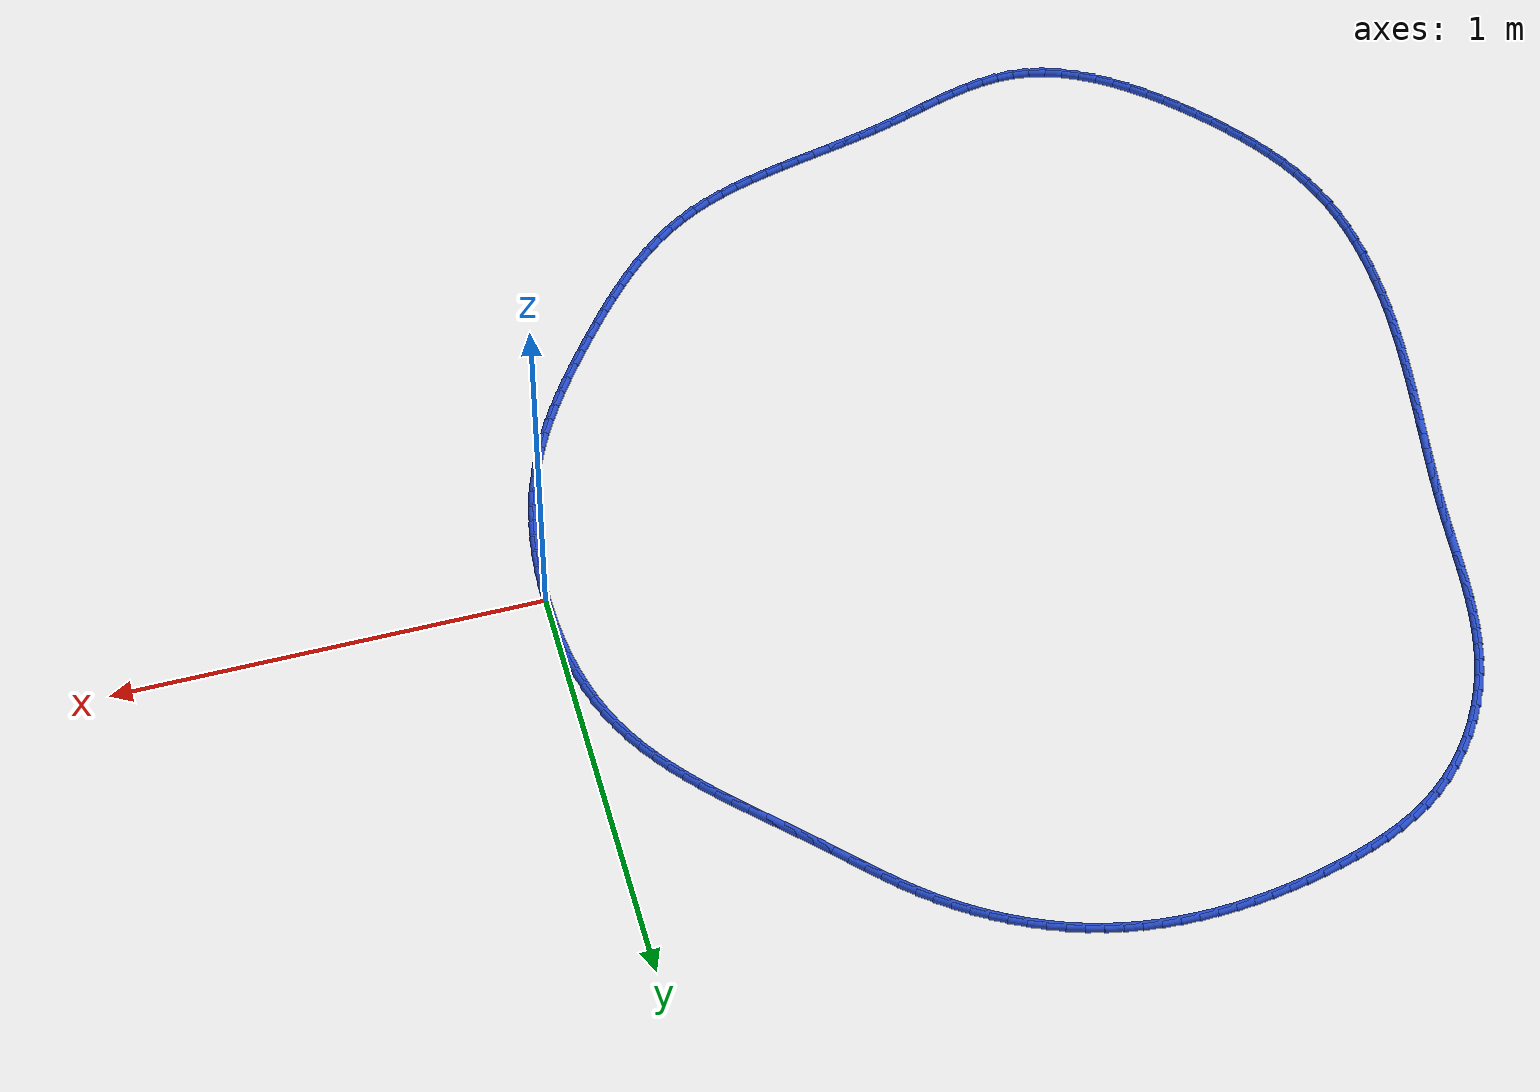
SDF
<sdf version="1.6">
 <world name="default">
  <light name="sun" type="directional">
   <pose>0 0 10 0 -0 0</pose>
   <diffuse>0.8 0.8 0.8 1</diffuse>
   <specular>0.2 0.2 0.2 1</specular>
   <attenuation>
    <range>1000</range>
    <constant>0.9</constant>
    <linear>0.01</linear>
    <quadratic>0.001</quadratic>
   </attenuation>
   <direction>-0.5 0.1 -0.9</direction>
  </light>
  <model name="ground_plane">
   <static>1</static>
   <link name="link">
    <collision name="collision">
     <geometry><plane><normal>0 0 1</normal><size>100 100</size></plane></geometry>
     <surface><friction><ode><mu>100</mu><mu2>50</mu2></ode></friction></surface>
    </collision>
    <visual name="visual">
     <cast_shadows>0</cast_shadows>
     <geometry><plane><normal>0 0 1</normal><size>100 100</size></plane></geometry>
     <material>
      <script><uri>file://media/materials/scripts/gazebo.material</uri><name>Gazebo/WhiteGlow</name></script>
     </material>
    </visual>
   </link>
  </model>
  <gravity>0 0 -9.8</gravity>
  <magnetic_field>6e-06 2.3e-05 -4.2e-05</magnetic_field>
  <atmosphere type="adiabatic"/>
  <physics name="default_physics" default="0" type="ode">
   <max_step_size>0.001</max_step_size>
   <real_time_factor>1</real_time_factor>
   <real_time_update_rate>1000</real_time_update_rate>
  </physics>
  <scene><ambient>0.4 0.4 0.4 1</ambient><background>0.7 0.7 0.7 1</background><shadows>1</shadows></scene>
  <spherical_coordinates>
   <surface_model>EARTH_WGS84</surface_model>
   <latitude_deg>0</latitude_deg>
   <longitude_deg>0</longitude_deg>
   <elevation>0</elevation>
   <heading_deg>0</heading_deg>
  </spherical_coordinates>
  <model name="line">
   <link name="link_0">
    <pose>-9.540979117872439e-18 2.7755575615628914e-17 0.01 0 1.57 -1.5623964826857273</pose>
    <collision name="collision">
     <geometry><cylinder><radius>0.01</radius><length>0.08</length></cylinder></geometry>
    </collision>
    <visual name="visual">
     <material>
      <script><name>Gazebo/Blue</name><uri>file://media/materials/scripts/gazebo.material</uri></script>
     </material>
     <geometry><cylinder><radius>0.01</radius><length>0.08</length></cylinder></geometry>
    </visual>
   </link>
   <link name="link_1">
    <pose>-0.0003562288091940997 0.0424079811880335 0.01 0 1.57 -1.5247359570351855</pose>
    <collision name="collision">
     <geometry><cylinder><radius>0.01</radius><length>0.08</length></cylinder></geometry>
    </collision>
    <visual name="visual">
     <material>
      <script><name>Gazebo/Blue</name><uri>file://media/materials/scripts/gazebo.material</uri></script>
     </material>
     <geometry><cylinder><radius>0.01</radius><length>0.08</length></cylinder></geometry>
    </visual>
   </link>
   <link name="link_2">
    <pose>-0.0023086248198908523 0.0847657633475471 0.01 0 1.57 -1.4842057410398612</pose>
    <collision name="collision">
     <geometry><cylinder><radius>0.01</radius><length>0.08</length></cylinder></geometry>
    </collision>
    <visual name="visual">
     <material>
      <script><name>Gazebo/Blue</name><uri>file://media/materials/scripts/gazebo.material</uri></script>
     </material>
     <geometry><cylinder><radius>0.01</radius><length>0.08</length></cylinder></geometry>
    </visual>
   </link>
   <link name="link_3">
    <pose>-0.00596728725873864 0.12691253602375624 0.01 0 1.57 -1.440479015036481</pose>
    <collision name="collision">
     <geometry><cylinder><radius>0.01</radius><length>0.08</length></cylinder></geometry>
    </collision>
    <visual name="visual">
     <material>
      <script><name>Gazebo/Blue</name><uri>file://media/materials/scripts/gazebo.material</uri></script>
     </material>
     <geometry><cylinder><radius>0.01</radius><length>0.08</length></cylinder></geometry>
    </visual>
   </link>
   <link name="link_4">
    <pose>-0.011442315352385822 0.16868748876187634 0.01 0 1.57 -1.3932230657818718</pose>
    <collision name="collision">
     <geometry><cylinder><radius>0.01</radius><length>0.08</length></cylinder></geometry>
    </collision>
    <visual name="visual">
     <material>
      <script><name>Gazebo/Blue</name><uri>file://media/materials/scripts/gazebo.material</uri></script>
     </material>
     <geometry><cylinder><radius>0.01</radius><length>0.08</length></cylinder></geometry>
    </visual>
   </link>
   <link name="link_5">
    <pose>-0.018843808327480775 0.2099298111071229 0.01 0 1.57 -1.3421105455488131</pose>
    <collision name="collision">
     <geometry><cylinder><radius>0.01</radius><length>0.08</length></cylinder></geometry>
    </collision>
    <visual name="visual">
     <material>
      <script><name>Gazebo/Blue</name><uri>file://media/materials/scripts/gazebo.material</uri></script>
     </material>
     <geometry><cylinder><radius>0.01</radius><length>0.08</length></cylinder></geometry>
    </visual>
   </link>
   <link name="link_6">
    <pose>-0.02828186541067184 0.250478692604711 0.01 0 1.57 -1.286836920057177</pose>
    <collision name="collision">
     <geometry><cylinder><radius>0.01</radius><length>0.08</length></cylinder></geometry>
    </collision>
    <visual name="visual">
     <material>
      <script><name>Gazebo/Blue</name><uri>file://media/materials/scripts/gazebo.material</uri></script>
     </material>
     <geometry><cylinder><radius>0.01</radius><length>0.08</length></cylinder></geometry>
    </visual>
   </link>
   <link name="link_7">
    <pose>-0.039866585828607394 0.29017332279985636 0.01 0 1.57 -1.227145391008153</pose>
    <collision name="collision">
     <geometry><cylinder><radius>0.01</radius><length>0.08</length></cylinder></geometry>
    </collision>
    <visual name="visual">
     <material>
      <script><name>Gazebo/Blue</name><uri>file://media/materials/scripts/gazebo.material</uri></script>
     </material>
     <geometry><cylinder><radius>0.01</radius><length>0.08</length></cylinder></geometry>
    </visual>
   </link>
   <link name="link_8">
    <pose>-0.05370806880793581 0.3288528912377743 0.01 0 1.57 -1.1628645254882457</pose>
    <collision name="collision">
     <geometry><cylinder><radius>0.01</radius><length>0.08</length></cylinder></geometry>
    </collision>
    <visual name="visual">
     <material>
      <script><name>Gazebo/Blue</name><uri>file://media/materials/scripts/gazebo.material</uri></script>
     </material>
     <geometry><cylinder><radius>0.01</radius><length>0.08</length></cylinder></geometry>
    </visual>
   </link>
   <link name="link_9">
    <pose>-0.06991626361049053 0.36635670991508085 0.01 0 1.57 -1.0965090194207292</pose>
    <collision name="collision">
     <geometry><cylinder><radius>0.01</radius><length>0.08</length></cylinder></geometry>
    </collision>
    <visual name="visual">
     <material>
      <script><name>Gazebo/Blue</name><uri>file://media/materials/scripts/gazebo.material</uri></script>
     </material>
     <geometry><cylinder><radius>0.01</radius><length>0.08</length></cylinder></geometry>
    </visual>
   </link>
   <link name="link_10">
    <pose>-0.08851828185614899 0.40259173059642406 0.01 0 1.57 -1.0351938888576513</pose>
    <collision name="collision">
     <geometry><cylinder><radius>0.01</radius><length>0.08</length></cylinder></geometry>
    </collision>
    <visual name="visual">
     <material>
      <script><name>Gazebo/Blue</name><uri>file://media/materials/scripts/gazebo.material</uri></script>
     </material>
     <geometry><cylinder><radius>0.01</radius><length>0.08</length></cylinder></geometry>
    </visual>
   </link>
   <link name="link_11">
    <pose>-0.10932107064573414 0.43764467690675574 0.01 0 1.57 -0.9804295119515052</pose>
    <collision name="collision">
     <geometry><cylinder><radius>0.01</radius><length>0.08</length></cylinder></geometry>
    </collision>
    <visual name="visual">
     <material>
      <script><name>Gazebo/Blue</name><uri>file://media/materials/scripts/gazebo.material</uri></script>
     </material>
     <geometry><cylinder><radius>0.01</radius><length>0.08</length></cylinder></geometry>
    </visual>
   </link>
   <link name="link_12">
    <pose>-0.13209540611197276 0.47163180730366855 0.01 0 1.57 -0.9323806596505106</pose>
    <collision name="collision">
     <geometry><cylinder><radius>0.01</radius><length>0.08</length></cylinder></geometry>
    </collision>
    <visual name="visual">
     <material>
      <script><name>Gazebo/Blue</name><uri>file://media/materials/scripts/gazebo.material</uri></script>
     </material>
     <geometry><cylinder><radius>0.01</radius><length>0.08</length></cylinder></geometry>
    </visual>
   </link>
   <link name="link_13">
    <pose>-0.1566120643875915 0.5046693802447554 0.01 0 1.57 -0.8910328413203374</pose>
    <collision name="collision">
     <geometry><cylinder><radius>0.01</radius><length>0.08</length></cylinder></geometry>
    </collision>
    <visual name="visual">
     <material>
      <script><name>Gazebo/Blue</name><uri>file://media/materials/scripts/gazebo.material</uri></script>
     </material>
     <geometry><cylinder><radius>0.01</radius><length>0.08</length></cylinder></geometry>
    </visual>
   </link>
   <link name="link_14">
    <pose>-0.18264182160531692 0.5368736541876082 0.01 0 1.57 -0.8562578924706724</pose>
    <collision name="collision">
     <geometry><cylinder><radius>0.01</radius><length>0.08</length></cylinder></geometry>
    </collision>
    <visual name="visual">
     <material>
      <script><name>Gazebo/Blue</name><uri>file://media/materials/scripts/gazebo.material</uri></script>
     </material>
     <geometry><cylinder><radius>0.01</radius><length>0.08</length></cylinder></geometry>
    </visual>
   </link>
   <link name="link_15">
    <pose>-0.2099554538978758 0.5683608875898203 0.01 0 1.57 -0.8278699339854914</pose>
    <collision name="collision">
     <geometry><cylinder><radius>0.01</radius><length>0.08</length></cylinder></geometry>
    </collision>
    <visual name="visual">
     <material>
      <script><name>Gazebo/Blue</name><uri>file://media/materials/scripts/gazebo.material</uri></script>
     </material>
     <geometry><cylinder><radius>0.01</radius><length>0.08</length></cylinder></geometry>
    </visual>
   </link>
   <link name="link_16">
    <pose>-0.2383237373979949 0.5992473389089841 0.01 0 1.57 -0.8056689649338641</pose>
    <collision name="collision">
     <geometry><cylinder><radius>0.01</radius><length>0.08</length></cylinder></geometry>
    </collision>
    <visual name="visual">
     <material>
      <script><name>Gazebo/Blue</name><uri>file://media/materials/scripts/gazebo.material</uri></script>
     </material>
     <geometry><cylinder><radius>0.01</radius><length>0.08</length></cylinder></geometry>
    </visual>
   </link>
   <link name="link_17">
    <pose>-0.26751744823840073 0.6296492666026922 0.01 0 1.57 -0.7894725915156587</pose>
    <collision name="collision">
     <geometry><cylinder><radius>0.01</radius><length>0.08</length></cylinder></geometry>
    </collision>
    <visual name="visual">
     <material>
      <script><name>Gazebo/Blue</name><uri>file://media/materials/scripts/gazebo.material</uri></script>
     </material>
     <geometry><cylinder><radius>0.01</radius><length>0.08</length></cylinder></geometry>
    </visual>
   </link>
   <link name="link_18">
    <pose>-0.2973073625518199 0.6596829291285371 0.01 0 1.57 -0.7791378650885057</pose>
    <collision name="collision">
     <geometry><cylinder><radius>0.01</radius><length>0.08</length></cylinder></geometry>
    </collision>
    <visual name="visual">
     <material>
      <script><name>Gazebo/Blue</name><uri>file://media/materials/scripts/gazebo.material</uri></script>
     </material>
     <geometry><cylinder><radius>0.01</radius><length>0.08</length></cylinder></geometry>
    </visual>
   </link>
   <link name="link_19">
    <pose>-0.32746425647097926 0.6894645849441114 0.01 0 1.57 -0.7745754951486501</pose>
    <collision name="collision">
     <geometry><cylinder><radius>0.01</radius><length>0.08</length></cylinder></geometry>
    </collision>
    <visual name="visual">
     <material>
      <script><name>Gazebo/Blue</name><uri>file://media/materials/scripts/gazebo.material</uri></script>
     </material>
     <geometry><cylinder><radius>0.01</radius><length>0.08</length></cylinder></geometry>
    </visual>
   </link>
   <link name="link_20">
    <pose>-0.3577589061286057 0.7191104925070084 0.01 0 1.57 -0.7757583546364858</pose>
    <collision name="collision">
     <geometry><cylinder><radius>0.01</radius><length>0.08</length></cylinder></geometry>
    </collision>
    <visual name="visual">
     <material>
      <script><name>Gazebo/Blue</name><uri>file://media/materials/scripts/gazebo.material</uri></script>
     </material>
     <geometry><cylinder><radius>0.01</radius><length>0.08</length></cylinder></geometry>
    </visual>
   </link>
   <link name="link_21">
    <pose>-0.38796208765742546 0.7487369102748199 0.01 0 1.57 -0.7827255534395113</pose>
    <collision name="collision">
     <geometry><cylinder><radius>0.01</radius><length>0.08</length></cylinder></geometry>
    </collision>
    <visual name="visual">
     <material>
      <script><name>Gazebo/Blue</name><uri>file://media/materials/scripts/gazebo.material</uri></script>
     </material>
     <geometry><cylinder><radius>0.01</radius><length>0.08</length></cylinder></geometry>
    </visual>
   </link>
   <link name="link_22">
    <pose>-0.41784457719016516 0.7784600967051386 0.01 0 1.57 -0.7942603477439405</pose>
    <collision name="collision">
     <geometry><cylinder><radius>0.01</radius><length>0.08</length></cylinder></geometry>
    </collision>
    <visual name="visual">
     <material>
      <script><name>Gazebo/Blue</name><uri>file://media/materials/scripts/gazebo.material</uri></script>
     </material>
     <geometry><cylinder><radius>0.01</radius><length>0.08</length></cylinder></geometry>
    </visual>
   </link>
   <link name="link_23">
    <pose>-0.44722399234699994 0.808364913408346 0.01 0 1.57 -0.8010249459513406</pose>
    <collision name="collision">
     <geometry><cylinder><radius>0.01</radius><length>0.08</length></cylinder></geometry>
    </collision>
    <visual name="visual">
     <material>
      <script><name>Gazebo/Blue</name><uri>file://media/materials/scripts/gazebo.material</uri></script>
     </material>
     <geometry><cylinder><radius>0.01</radius><length>0.08</length></cylinder></geometry>
    </visual>
   </link>
   <link name="link_24">
    <pose>-0.476250641501954 0.838313226497959 0.01 0 1.57 -0.7988324356967438</pose>
    <collision name="collision">
     <geometry><cylinder><radius>0.01</radius><length>0.08</length></cylinder></geometry>
    </collision>
    <visual name="visual">
     <material>
      <script><name>Gazebo/Blue</name><uri>file://media/materials/scripts/gazebo.material</uri></script>
     </material>
     <geometry><cylinder><radius>0.01</radius><length>0.08</length></cylinder></geometry>
    </visual>
   </link>
   <link name="link_25">
    <pose>-0.5052188235792384 0.8680703883013109 0.01 0 1.57 -0.7875572953811117</pose>
    <collision name="collision">
     <geometry><cylinder><radius>0.01</radius><length>0.08</length></cylinder></geometry>
    </collision>
    <visual name="visual">
     <material>
      <script><name>Gazebo/Blue</name><uri>file://media/materials/scripts/gazebo.material</uri></script>
     </material>
     <geometry><cylinder><radius>0.01</radius><length>0.08</length></cylinder></geometry>
    </visual>
   </link>
   <link name="link_26">
    <pose>-0.5344234138797878 0.8974013648127438 0.01 0 1.57 -0.7671465289753625</pose>
    <collision name="collision">
     <geometry><cylinder><radius>0.01</radius><length>0.08</length></cylinder></geometry>
    </collision>
    <visual name="visual">
     <material>
      <script><name>Gazebo/Blue</name><uri>file://media/materials/scripts/gazebo.material</uri></script>
     </material>
     <geometry><cylinder><radius>0.01</radius><length>0.08</length></cylinder></geometry>
    </visual>
   </link>
   <link name="link_27">
    <pose>-0.5641592877045366 0.9260711220265999 0.01 0 1.57 -0.7376329778385887</pose>
    <collision name="collision">
     <geometry><cylinder><radius>0.01</radius><length>0.08</length></cylinder></geometry>
    </collision>
    <visual name="visual">
     <material>
      <script><name>Gazebo/Blue</name><uri>file://media/materials/scripts/gazebo.material</uri></script>
     </material>
     <geometry><cylinder><radius>0.01</radius><length>0.08</length></cylinder></geometry>
    </visual>
   </link>
   <link name="link_28">
    <pose>-0.5947213203544199 0.9538446259372217 0.01 0 1.57 -0.6991984845940142</pose>
    <collision name="collision">
     <geometry><cylinder><radius>0.01</radius><length>0.08</length></cylinder></geometry>
    </collision>
    <visual name="visual">
     <material>
      <script><name>Gazebo/Blue</name><uri>file://media/materials/scripts/gazebo.material</uri></script>
     </material>
     <geometry><cylinder><radius>0.01</radius><length>0.08</length></cylinder></geometry>
    </visual>
   </link>
   <link name="link_29">
    <pose>-0.6264038226670672 0.9804870489868515 0.01 0 1.57 -0.6546484537541121</pose>
    <collision name="collision">
     <geometry><cylinder><radius>0.01</radius><length>0.08</length></cylinder></geometry>
    </collision>
    <visual name="visual">
     <material>
      <script><name>Gazebo/Blue</name><uri>file://media/materials/scripts/gazebo.material</uri></script>
     </material>
     <geometry><cylinder><radius>0.01</radius><length>0.08</length></cylinder></geometry>
    </visual>
   </link>
   <link name="link_30">
    <pose>-0.6593883280496291 1.0058048110530569 0.01 0 1.57 -0.6094801853400681</pose>
    <collision name="collision">
     <geometry><cylinder><radius>0.01</radius><length>0.08</length></cylinder></geometry>
    </collision>
    <visual name="visual">
     <material>
      <script><name>Gazebo/Blue</name><uri>file://media/materials/scripts/gazebo.material</uri></script>
     </material>
     <geometry><cylinder><radius>0.01</radius><length>0.08</length></cylinder></geometry>
    </visual>
   </link>
   <link name="link_31">
    <pose>-0.6936080502866613 1.0296951529119627 0.01 0 1.57 -0.564180259478845</pose>
    <collision name="collision">
     <geometry><cylinder><radius>0.01</radius><length>0.08</length></cylinder></geometry>
    </collision>
    <visual name="visual">
     <material>
      <script><name>Gazebo/Blue</name><uri>file://media/materials/scripts/gazebo.material</uri></script>
     </material>
     <geometry><cylinder><radius>0.01</radius><length>0.08</length></cylinder></geometry>
    </visual>
   </link>
   <link name="link_32">
    <pose>-0.7289631097116125 1.0520674190024433 0.01 0 1.57 -0.5185027385650475</pose>
    <collision name="collision">
     <geometry><cylinder><radius>0.01</radius><length>0.08</length></cylinder></geometry>
    </collision>
    <visual name="visual">
     <material>
      <script><name>Gazebo/Blue</name><uri>file://media/materials/scripts/gazebo.material</uri></script>
     </material>
     <geometry><cylinder><radius>0.01</radius><length>0.08</length></cylinder></geometry>
    </visual>
   </link>
   <link name="link_33">
    <pose>-0.7653536266579317 1.072830953763373 0.01 0 1.57 -0.47220728353582436</pose>
    <collision name="collision">
     <geometry><cylinder><radius>0.01</radius><length>0.08</length></cylinder></geometry>
    </collision>
    <visual name="visual">
     <material>
      <script><name>Gazebo/Blue</name><uri>file://media/materials/scripts/gazebo.material</uri></script>
     </material>
     <geometry><cylinder><radius>0.01</radius><length>0.08</length></cylinder></geometry>
    </visual>
   </link>
   <link name="link_34">
    <pose>-0.8026797214590681 1.0918951016336251 0.01 0 1.57 -0.42505917483939354</pose>
    <collision name="collision">
     <geometry><cylinder><radius>0.01</radius><length>0.08</length></cylinder></geometry>
    </collision>
    <visual name="visual">
     <material>
      <script><name>Gazebo/Blue</name><uri>file://media/materials/scripts/gazebo.material</uri></script>
     </material>
     <geometry><cylinder><radius>0.01</radius><length>0.08</length></cylinder></geometry>
    </visual>
   </link>
   <link name="link_35">
    <pose>-0.8408415144484703 1.1091692070520742 0.01 0 1.57 -0.3768300582452592</pose>
    <collision name="collision">
     <geometry><cylinder><radius>0.01</radius><length>0.08</length></cylinder></geometry>
    </collision>
    <visual name="visual">
     <material>
      <script><name>Gazebo/Blue</name><uri>file://media/materials/scripts/gazebo.material</uri></script>
     </material>
     <geometry><cylinder><radius>0.01</radius><length>0.08</length></cylinder></geometry>
    </visual>
   </link>
   <link name="link_36">
    <pose>-0.8797391259595877 1.124562614457594 0.01 0 1.57 -0.3272996272543197</pose>
    <collision name="collision">
     <geometry><cylinder><radius>0.01</radius><length>0.08</length></cylinder></geometry>
    </collision>
    <visual name="visual">
     <material>
      <script><name>Gazebo/Blue</name><uri>file://media/materials/scripts/gazebo.material</uri></script>
     </material>
     <geometry><cylinder><radius>0.01</radius><length>0.08</length></cylinder></geometry>
    </visual>
   </link>
   <link name="link_37">
    <pose>-0.9192726763258692 1.1379846682890589 0.01 0 1.57 -0.27625979984172294</pose>
    <collision name="collision">
     <geometry><cylinder><radius>0.01</radius><length>0.08</length></cylinder></geometry>
    </collision>
    <visual name="visual">
     <material>
      <script><name>Gazebo/Blue</name><uri>file://media/materials/scripts/gazebo.material</uri></script>
     </material>
     <geometry><cylinder><radius>0.01</radius><length>0.08</length></cylinder></geometry>
    </visual>
   </link>
   <link name="link_38">
    <pose>-0.9593423002767159 1.1493447749007104 0.01 0 1.57 -0.22440984350333143</pose>
    <collision name="collision">
     <geometry><cylinder><radius>0.01</radius><length>0.08</length></cylinder></geometry>
    </collision>
    <visual name="visual">
     <material>
      <script><name>Gazebo/Blue</name><uri>file://media/materials/scripts/gazebo.material</uri></script>
     </material>
     <geometry><cylinder><radius>0.01</radius><length>0.08</length></cylinder></geometry>
    </visual>
   </link>
   <link name="link_39">
    <pose>-0.9998574798112231 1.1585925421992922 0.01 0 1.57 -0.17413968294643584</pose>
    <collision name="collision">
     <geometry><cylinder><radius>0.01</radius><length>0.08</length></cylinder></geometry>
    </collision>
    <visual name="visual">
     <material>
      <script><name>Gazebo/Blue</name><uri>file://media/materials/scripts/gazebo.material</uri></script>
     </material>
     <geometry><cylinder><radius>0.01</radius><length>0.08</length></cylinder></geometry>
    </visual>
   </link>
   <link name="link_40">
    <pose>-1.0407531312372884 1.1657869681845168 0.01 0 1.57 -0.12594567128181372</pose>
    <collision name="collision">
     <geometry><cylinder><radius>0.01</radius><length>0.08</length></cylinder></geometry>
    </collision>
    <visual name="visual">
     <material>
      <script><name>Gazebo/Blue</name><uri>file://media/materials/scripts/gazebo.material</uri></script>
     </material>
     <geometry><cylinder><radius>0.01</radius><length>0.08</length></cylinder></geometry>
    </visual>
   </link>
   <link name="link_41">
    <pose>-1.081968456231779 1.1710054817446083 0.01 0 1.57 -0.07988015375008775</pose>
    <collision name="collision">
     <geometry><cylinder><radius>0.01</radius><length>0.08</length></cylinder></geometry>
    </collision>
    <visual name="visual">
     <material>
      <script><name>Gazebo/Blue</name><uri>file://media/materials/scripts/gazebo.material</uri></script>
     </material>
     <geometry><cylinder><radius>0.01</radius><length>0.08</length></cylinder></geometry>
    </visual>
   </link>
   <link name="link_42">
    <pose>-1.123442656471563 1.1743255117677915 0.01 0 1.57 -0.03595506363216738</pose>
    <collision name="collision">
     <geometry><cylinder><radius>0.01</radius><length>0.08</length></cylinder></geometry>
    </collision>
    <visual name="visual">
     <material>
      <script><name>Gazebo/Blue</name><uri>file://media/materials/scripts/gazebo.material</uri></script>
     </material>
     <geometry><cylinder><radius>0.01</radius><length>0.08</length></cylinder></geometry>
    </visual>
   </link>
   <link name="link_43">
    <pose>-1.1651149336335065 1.17582448714229 0.01 0 1.57 0.005851475559722349</pose>
    <collision name="collision">
     <geometry><cylinder><radius>0.01</radius><length>0.08</length></cylinder></geometry>
    </collision>
    <visual name="visual">
     <material>
      <script><name>Gazebo/Blue</name><uri>file://media/materials/scripts/gazebo.material</uri></script>
     </material>
     <geometry><cylinder><radius>0.01</radius><length>0.08</length></cylinder></geometry>
    </visual>
   </link>
   <link name="link_44">
    <pose>-1.2069244893944777 1.1755798367563282 0.01 0 1.57 0.04558854154042361</pose>
    <collision name="collision">
     <geometry><cylinder><radius>0.01</radius><length>0.08</length></cylinder></geometry>
    </collision>
    <visual name="visual">
     <material>
      <script><name>Gazebo/Blue</name><uri>file://media/materials/scripts/gazebo.material</uri></script>
     </material>
     <geometry><cylinder><radius>0.01</radius><length>0.08</length></cylinder></geometry>
    </visual>
   </link>
   <link name="link_45">
    <pose>-1.2488105254313435 1.1736689894981298 0.01 0 1.57 0.08332622334259836</pose>
    <collision name="collision">
     <geometry><cylinder><radius>0.01</radius><length>0.08</length></cylinder></geometry>
    </collision>
    <visual name="visual">
     <material>
      <script><name>Gazebo/Blue</name><uri>file://media/materials/scripts/gazebo.material</uri></script>
     </material>
     <geometry><cylinder><radius>0.01</radius><length>0.08</length></cylinder></geometry>
    </visual>
   </link>
   <link name="link_46">
    <pose>-1.2907122434209712 1.1701693742559198 0.01 0 1.57 0.1191501121461086</pose>
    <collision name="collision">
     <geometry><cylinder><radius>0.01</radius><length>0.08</length></cylinder></geometry>
    </collision>
    <visual name="visual">
     <material>
      <script><name>Gazebo/Blue</name><uri>file://media/materials/scripts/gazebo.material</uri></script>
     </material>
     <geometry><cylinder><radius>0.01</radius><length>0.08</length></cylinder></geometry>
    </visual>
   </link>
   <link name="link_47">
    <pose>-1.3325688450402284 1.1651584199179215 0.01 0 1.57 0.15315660077320795</pose>
    <collision name="collision">
     <geometry><cylinder><radius>0.01</radius><length>0.08</length></cylinder></geometry>
    </collision>
    <visual name="visual">
     <material>
      <script><name>Gazebo/Blue</name><uri>file://media/materials/scripts/gazebo.material</uri></script>
     </material>
     <geometry><cylinder><radius>0.01</radius><length>0.08</length></cylinder></geometry>
    </visual>
   </link>
   <link name="link_48">
    <pose>-1.3743195319659818 1.15871355537236 0.01 0 1.57 0.18544902056028048</pose>
    <collision name="collision">
     <geometry><cylinder><radius>0.01</radius><length>0.08</length></cylinder></geometry>
    </collision>
    <visual name="visual">
     <material>
      <script><name>Gazebo/Blue</name><uri>file://media/materials/scripts/gazebo.material</uri></script>
     </material>
     <geometry><cylinder><radius>0.01</radius><length>0.08</length></cylinder></geometry>
    </visual>
   </link>
   <link name="link_49">
    <pose>-1.4159035058750993 1.150912209507459 0.01 0 1.57 0.21613457849729314</pose>
    <collision name="collision">
     <geometry><cylinder><radius>0.01</radius><length>0.08</length></cylinder></geometry>
    </collision>
    <visual name="visual">
     <material>
      <script><name>Gazebo/Blue</name><uri>file://media/materials/scripts/gazebo.material</uri></script>
     </material>
     <geometry><cylinder><radius>0.01</radius><length>0.08</length></cylinder></geometry>
    </visual>
   </link>
   <link name="link_50">
    <pose>-1.4572599684444478 1.1418318112114423 0.01 0 1.57 0.24533033604755863</pose>
    <collision name="collision">
     <geometry><cylinder><radius>0.01</radius><length>0.08</length></cylinder></geometry>
    </collision>
    <visual name="visual">
     <material>
      <script><name>Gazebo/Blue</name><uri>file://media/materials/scripts/gazebo.material</uri></script>
     </material>
     <geometry><cylinder><radius>0.01</radius><length>0.08</length></cylinder></geometry>
    </visual>
   </link>
   <link name="link_51">
    <pose>-1.4983279653092965 1.1315494654865548 0.01 0 1.57 0.2753581099417407</pose>
    <collision name="collision">
     <geometry><cylinder><radius>0.01</radius><length>0.08</length></cylinder></geometry>
    </collision>
    <visual name="visual">
     <material>
      <script><name>Gazebo/Blue</name><uri>file://media/materials/scripts/gazebo.material</uri></script>
     </material>
     <geometry><cylinder><radius>0.01</radius><length>0.08</length></cylinder></geometry>
    </visual>
   </link>
   <link name="link_52">
    <pose>-1.5390053042433967 1.120056682433804 0.01 0 1.57 0.31159260127298016</pose>
    <collision name="collision">
     <geometry><cylinder><radius>0.01</radius><length>0.08</length></cylinder></geometry>
    </collision>
    <visual name="visual">
     <material>
      <script><name>Gazebo/Blue</name><uri>file://media/materials/scripts/gazebo.material</uri></script>
     </material>
     <geometry><cylinder><radius>0.01</radius><length>0.08</length></cylinder></geometry>
    </visual>
   </link>
   <link name="link_53">
    <pose>-1.5790934151281 1.1071449264709938 0.01 0 1.57 0.35509095068433766</pose>
    <collision name="collision">
     <geometry><cylinder><radius>0.01</radius><length>0.08</length></cylinder></geometry>
    </collision>
    <visual name="visual">
     <material>
      <script><name>Gazebo/Blue</name><uri>file://media/materials/scripts/gazebo.material</uri></script>
     </material>
     <geometry><cylinder><radius>0.01</radius><length>0.08</length></cylinder></geometry>
    </visual>
   </link>
   <link name="link_54">
    <pose>-1.618379981838624 1.0925771302736345 0.01 0 1.57 0.40617832132936155</pose>
    <collision name="collision">
     <geometry><cylinder><radius>0.01</radius><length>0.08</length></cylinder></geometry>
    </collision>
    <visual name="visual">
     <material>
      <script><name>Gazebo/Blue</name><uri>file://media/materials/scripts/gazebo.material</uri></script>
     </material>
     <geometry><cylinder><radius>0.01</radius><length>0.08</length></cylinder></geometry>
    </visual>
   </link>
   <link name="link_55">
    <pose>-1.6566526882501853 1.076116226517235 0.01 0 1.57 0.46511093592235686</pose>
    <collision name="collision">
     <geometry><cylinder><radius>0.01</radius><length>0.08</length></cylinder></geometry>
    </collision>
    <visual name="visual">
     <material>
      <script><name>Gazebo/Blue</name><uri>file://media/materials/scripts/gazebo.material</uri></script>
     </material>
     <geometry><cylinder><radius>0.01</radius><length>0.08</length></cylinder></geometry>
    </visual>
   </link>
   <link name="link_56">
    <pose>-1.6936992182379995 1.0575251478773058 0.01 0 1.57 0.5319830866198535</pose>
    <collision name="collision">
     <geometry><cylinder><radius>0.01</radius><length>0.08</length></cylinder></geometry>
    </collision>
    <visual name="visual">
     <material>
      <script><name>Gazebo/Blue</name><uri>file://media/materials/scripts/gazebo.material</uri></script>
     </material>
     <geometry><cylinder><radius>0.01</radius><length>0.08</length></cylinder></geometry>
    </visual>
   </link>
   <link name="link_57">
    <pose>-1.7293072556772855 1.0365668270293573 0.01 0 1.57 0.6066144839632988</pose>
    <collision name="collision">
     <geometry><cylinder><radius>0.01</radius><length>0.08</length></cylinder></geometry>
    </collision>
    <visual name="visual">
     <material>
      <script><name>Gazebo/Blue</name><uri>file://media/materials/scripts/gazebo.material</uri></script>
     </material>
     <geometry><cylinder><radius>0.01</radius><length>0.08</length></cylinder></geometry>
    </visual>
   </link>
   <link name="link_58">
    <pose>-1.7632644844432581 1.013004196648898 0.01 0 1.57 0.6865693805805728</pose>
    <collision name="collision">
     <geometry><cylinder><radius>0.01</radius><length>0.08</length></cylinder></geometry>
    </collision>
    <visual name="visual">
     <material>
      <script><name>Gazebo/Blue</name><uri>file://media/materials/scripts/gazebo.material</uri></script>
     </material>
     <geometry><cylinder><radius>0.01</radius><length>0.08</length></cylinder></geometry>
    </visual>
   </link>
   <link name="link_59">
    <pose>-1.7953786654017523 0.9866838995297144 0.01 0 1.57 0.7638899788799208</pose>
    <collision name="collision">
     <geometry><cylinder><radius>0.01</radius><length>0.08</length></cylinder></geometry>
    </collision>
    <visual name="visual">
     <material>
      <script><name>Gazebo/Blue</name><uri>file://media/materials/scripts/gazebo.material</uri></script>
     </material>
     <geometry><cylinder><radius>0.01</radius><length>0.08</length></cylinder></geometry>
    </visual>
   </link>
   <link name="link_60">
    <pose>-1.8255393289238953 0.9577935127764157 0.01 0 1.57 0.8370963599257377</pose>
    <collision name="collision">
     <geometry><cylinder><radius>0.01</radius><length>0.08</length></cylinder></geometry>
    </collision>
    <visual name="visual">
     <material>
      <script><name>Gazebo/Blue</name><uri>file://media/materials/scripts/gazebo.material</uri></script>
     </material>
     <geometry><cylinder><radius>0.01</radius><length>0.08</length></cylinder></geometry>
    </visual>
   </link>
   <link name="link_61">
    <pose>-1.8536568197680543 0.9266073981542535 0.01 0 1.57 0.9068211389162819</pose>
    <collision name="collision">
     <geometry><cylinder><radius>0.01</radius><length>0.08</length></cylinder></geometry>
    </collision>
    <visual name="visual">
     <material>
      <script><name>Gazebo/Blue</name><uri>file://media/materials/scripts/gazebo.material</uri></script>
     </material>
     <geometry><cylinder><radius>0.01</radius><length>0.08</length></cylinder></geometry>
    </visual>
   </link>
   <link name="link_62">
    <pose>-1.8796414826970353 0.8933999174469992 0.01 0 1.57 0.9737540779613557</pose>
    <collision name="collision">
     <geometry><cylinder><radius>0.01</radius><length>0.08</length></cylinder></geometry>
    </collision>
    <visual name="visual">
     <material>
      <script><name>Gazebo/Blue</name><uri>file://media/materials/scripts/gazebo.material</uri></script>
     </material>
     <geometry><cylinder><radius>0.01</radius><length>0.08</length></cylinder></geometry>
    </visual>
   </link>
   <link name="link_63">
    <pose>-1.903403662473646 0.8584454324384238 0.01 0 1.57 1.0386171794501016</pose>
    <collision name="collision">
     <geometry><cylinder><radius>0.01</radius><length>0.08</length></cylinder></geometry>
    </collision>
    <visual name="visual">
     <material>
      <script><name>Gazebo/Blue</name><uri>file://media/materials/scripts/gazebo.material</uri></script>
     </material>
     <geometry><cylinder><radius>0.01</radius><length>0.08</length></cylinder></geometry>
    </visual>
   </link>
   <link name="link_64">
    <pose>-1.9248537038606925 0.8220183049122984 0.01 0 1.57 1.1021530866560902</pose>
    <collision name="collision">
     <geometry><cylinder><radius>0.01</radius><length>0.08</length></cylinder></geometry>
    </collision>
    <visual name="visual">
     <material>
      <script><name>Gazebo/Blue</name><uri>file://media/materials/scripts/gazebo.material</uri></script>
     </material>
     <geometry><cylinder><radius>0.01</radius><length>0.08</length></cylinder></geometry>
    </visual>
   </link>
   <link name="link_65">
    <pose>-1.9439019516209832 0.7843928966523953 0.01 0 1.57 1.165123325051818</pose>
    <collision name="collision">
     <geometry><cylinder><radius>0.01</radius><length>0.08</length></cylinder></geometry>
    </collision>
    <visual name="visual">
     <material>
      <script><name>Gazebo/Blue</name><uri>file://media/materials/scripts/gazebo.material</uri></script>
     </material>
     <geometry><cylinder><radius>0.01</radius><length>0.08</length></cylinder></geometry>
    </visual>
   </link>
   <link name="link_66">
    <pose>-1.960458750517325 0.7458435694424842 0.01 0 1.57 1.2278232726069838</pose>
    <collision name="collision">
     <geometry><cylinder><radius>0.01</radius><length>0.08</length></cylinder></geometry>
    </collision>
    <visual name="visual">
     <material>
      <script><name>Gazebo/Blue</name><uri>file://media/materials/scripts/gazebo.material</uri></script>
     </material>
     <geometry><cylinder><radius>0.01</radius><length>0.08</length></cylinder></geometry>
    </visual>
   </link>
   <link name="link_67">
    <pose>-1.9744612939809378 0.7066301480224619 0.01 0 1.57 1.2862970459717007</pose>
    <collision name="collision">
     <geometry><cylinder><radius>0.01</radius><length>0.08</length></cylinder></geometry>
    </collision>
    <visual name="visual">
     <material>
      <script><name>Gazebo/Blue</name><uri>file://media/materials/scripts/gazebo.material</uri></script>
     </material>
     <geometry><cylinder><radius>0.01</radius><length>0.08</length></cylinder></geometry>
    </visual>
   </link>
   <link name="link_68">
    <pose>-1.9860843980284681 0.6668837978670077 0.01 0 1.57 1.3378191165385243</pose>
    <collision name="collision">
     <geometry><cylinder><radius>0.01</radius><length>0.08</length></cylinder></geometry>
    </collision>
    <visual name="visual">
     <material>
      <script><name>Gazebo/Blue</name><uri>file://media/materials/scripts/gazebo.material</uri></script>
     </material>
     <geometry><cylinder><radius>0.01</radius><length>0.08</length></cylinder></geometry>
    </visual>
   </link>
   <link name="link_69">
    <pose>-1.99562691934425 0.6266685234057644 0.01 0 1.57 1.381990938745188</pose>
    <collision name="collision">
     <geometry><cylinder><radius>0.01</radius><length>0.08</length></cylinder></geometry>
    </collision>
    <visual name="visual">
     <material>
      <script><name>Gazebo/Blue</name><uri>file://media/materials/scripts/gazebo.material</uri></script>
     </material>
     <geometry><cylinder><radius>0.01</radius><length>0.08</length></cylinder></geometry>
    </visual>
   </link>
   <link name="link_70">
    <pose>-2.003388791272513 0.5860477461175947 0.01 0 1.57 1.4186436062493344</pose>
    <collision name="collision">
     <geometry><cylinder><radius>0.01</radius><length>0.08</length></cylinder></geometry>
    </collision>
    <visual name="visual">
     <material>
      <script><name>Gazebo/Blue</name><uri>file://media/materials/scripts/gazebo.material</uri></script>
     </material>
     <geometry><cylinder><radius>0.01</radius><length>0.08</length></cylinder></geometry>
    </visual>
   </link>
   <link name="link_71">
    <pose>-2.0096699471574895 0.5450848874813611 0.01 0 1.57 1.4477502582174562</pose>
    <collision name="collision">
     <geometry><cylinder><radius>0.01</radius><length>0.08</length></cylinder></geometry>
    </collision>
    <visual name="visual">
     <material>
      <script><name>Gazebo/Blue</name><uri>file://media/materials/scripts/gazebo.material</uri></script>
     </material>
     <geometry><cylinder><radius>0.01</radius><length>0.08</length></cylinder></geometry>
    </visual>
   </link>
   <link name="link_72">
    <pose>-2.0147703203434126 0.5038433689759272 0.01 0 1.57 1.4693642946234513</pose>
    <collision name="collision">
     <geometry><cylinder><radius>0.01</radius><length>0.08</length></cylinder></geometry>
    </collision>
    <visual name="visual">
     <material>
      <script><name>Gazebo/Blue</name><uri>file://media/materials/scripts/gazebo.material</uri></script>
     </material>
     <geometry><cylinder><radius>0.01</radius><length>0.08</length></cylinder></geometry>
    </visual>
   </link>
   <link name="link_73">
    <pose>-2.0189898441745124 0.4623866120801559 0.01 0 1.57 1.4835697119463425</pose>
    <collision name="collision">
     <geometry><cylinder><radius>0.01</radius><length>0.08</length></cylinder></geometry>
    </collision>
    <visual name="visual">
     <material>
      <script><name>Gazebo/Blue</name><uri>file://media/materials/scripts/gazebo.material</uri></script>
     </material>
     <geometry><cylinder><radius>0.01</radius><length>0.08</length></cylinder></geometry>
    </visual>
   </link>
   <link name="link_74">
    <pose>-2.022628451995021 0.42077803827290927 0.01 0 1.57 1.4904452565802997</pose>
    <collision name="collision">
     <geometry><cylinder><radius>0.01</radius><length>0.08</length></cylinder></geometry>
    </collision>
    <visual name="visual">
     <material>
      <script><name>Gazebo/Blue</name><uri>file://media/materials/scripts/gazebo.material</uri></script>
     </material>
     <geometry><cylinder><radius>0.01</radius><length>0.08</length></cylinder></geometry>
    </visual>
   </link>
   <link name="link_75">
    <pose>-2.02598607714917 0.37908106903305133 0.01 0 1.57 1.4900418721017965</pose>
    <collision name="collision">
     <geometry><cylinder><radius>0.01</radius><length>0.08</length></cylinder></geometry>
    </collision>
    <visual name="visual">
     <material>
      <script><name>Gazebo/Blue</name><uri>file://media/materials/scripts/gazebo.material</uri></script>
     </material>
     <geometry><cylinder><radius>0.01</radius><length>0.08</length></cylinder></geometry>
    </visual>
   </link>
   <link name="link_76">
    <pose>-2.029362652981191 0.3373591258394445 0.01 0 1.57 1.4823722778581816</pose>
    <collision name="collision">
     <geometry><cylinder><radius>0.01</radius><length>0.08</length></cylinder></geometry>
    </collision>
    <visual name="visual">
     <material>
      <script><name>Gazebo/Blue</name><uri>file://media/materials/scripts/gazebo.material</uri></script>
     </material>
     <geometry><cylinder><radius>0.01</radius><length>0.08</length></cylinder></geometry>
    </visual>
   </link>
   <link name="link_77">
    <pose>-2.0330581128353153 0.29567563017095144 0.01 0 1.57 1.4684773141866665</pose>
    <collision name="collision">
     <geometry><cylinder><radius>0.01</radius><length>0.08</length></cylinder></geometry>
    </collision>
    <visual name="visual">
     <material>
      <script><name>Gazebo/Blue</name><uri>file://media/materials/scripts/gazebo.material</uri></script>
     </material>
     <geometry><cylinder><radius>0.01</radius><length>0.08</length></cylinder></geometry>
    </visual>
   </link>
   <link name="link_78">
    <pose>-2.037328428090602 0.2540860711830503 0.01 0 1.57 1.4549609807632753</pose>
    <collision name="collision">
     <geometry><cylinder><radius>0.01</radius><length>0.08</length></cylinder></geometry>
    </collision>
    <visual name="visual">
     <material>
      <script><name>Gazebo/Blue</name><uri>file://media/materials/scripts/gazebo.material</uri></script>
     </material>
     <geometry><cylinder><radius>0.01</radius><length>0.08</length></cylinder></geometry>
    </visual>
   </link>
   <link name="link_79">
    <pose>-2.0421559894624948 0.21259657421667486 0.01 0 1.57 1.44437653615921</pose>
    <collision name="collision">
     <geometry><cylinder><radius>0.01</radius><length>0.08</length></cylinder></geometry>
    </collision>
    <visual name="visual">
     <material>
      <script><name>Gazebo/Blue</name><uri>file://media/materials/scripts/gazebo.material</uri></script>
     </material>
     <geometry><cylinder><radius>0.01</radius><length>0.08</length></cylinder></geometry>
    </visual>
   </link>
   <link name="link_80">
    <pose>-2.0474181184641007 0.17119430634081964 0.01 0 1.57 1.43673751962326</pose>
    <collision name="collision">
     <geometry><cylinder><radius>0.01</radius><length>0.08</length></cylinder></geometry>
    </collision>
    <visual name="visual">
     <material>
      <script><name>Gazebo/Blue</name><uri>file://media/materials/scripts/gazebo.material</uri></script>
     </material>
     <geometry><cylinder><radius>0.01</radius><length>0.08</length></cylinder></geometry>
    </visual>
   </link>
   <link name="link_81">
    <pose>-2.0529919193235413 0.1298663954184337 0.01 0 1.57 1.4320503162291487</pose>
    <collision name="collision">
     <geometry><cylinder><radius>0.01</radius><length>0.08</length></cylinder></geometry>
    </collision>
    <visual name="visual">
     <material>
      <script><name>Gazebo/Blue</name><uri>file://media/materials/scripts/gazebo.material</uri></script>
     </material>
     <geometry><cylinder><radius>0.01</radius><length>0.08</length></cylinder></geometry>
    </visual>
   </link>
   <link name="link_82">
    <pose>-2.058754496268939 0.08859996931246641 0.01 0 1.57 1.430321415375783</pose>
    <collision name="collision">
     <geometry><cylinder><radius>0.01</radius><length>0.08</length></cylinder></geometry>
    </collision>
    <visual name="visual">
     <material>
      <script><name>Gazebo/Blue</name><uri>file://media/materials/scripts/gazebo.material</uri></script>
     </material>
     <geometry><cylinder><radius>0.01</radius><length>0.08</length></cylinder></geometry>
    </visual>
   </link>
   <link name="link_83">
    <pose>-2.0645829535284164 0.04738215588586791 0.01 0 1.57 1.4315586471073556</pose>
    <collision name="collision">
     <geometry><cylinder><radius>0.01</radius><length>0.08</length></cylinder></geometry>
    </collision>
    <visual name="visual">
     <material>
      <script><name>Gazebo/Blue</name><uri>file://media/materials/scripts/gazebo.material</uri></script>
     </material>
     <geometry><cylinder><radius>0.01</radius><length>0.08</length></cylinder></geometry>
    </visual>
   </link>
   <link name="link_84">
    <pose>-2.0703543953300962 0.006200083001587 0.01 0 1.57 1.4357716512332173</pose>
    <collision name="collision">
     <geometry><cylinder><radius>0.01</radius><length>0.08</length></cylinder></geometry>
    </collision>
    <visual name="visual">
     <material>
      <script><name>Gazebo/Blue</name><uri>file://media/materials/scripts/gazebo.material</uri></script>
     </material>
     <geometry><cylinder><radius>0.01</radius><length>0.08</length></cylinder></geometry>
    </visual>
   </link>
   <link name="link_85">
    <pose>-2.0759459259021007 -0.03495912147742601 0.01 0 1.57 1.4429715660285354</pose>
    <collision name="collision">
     <geometry><cylinder><radius>0.01</radius><length>0.08</length></cylinder></geometry>
    </collision>
    <visual name="visual">
     <material>
      <script><name>Gazebo/Blue</name><uri>file://media/materials/scripts/gazebo.material</uri></script>
     </material>
     <geometry><cylinder><radius>0.01</radius><length>0.08</length></cylinder></geometry>
    </visual>
   </link>
   <link name="link_86">
    <pose>-2.081234649472552 -0.07610832968822191 0.01 0 1.57 1.4531699177430342</pose>
    <collision name="collision">
     <geometry><cylinder><radius>0.01</radius><length>0.08</length></cylinder></geometry>
    </collision>
    <visual name="visual">
     <material>
      <script><name>Gazebo/Blue</name><uri>file://media/materials/scripts/gazebo.material</uri></script>
     </material>
     <geometry><cylinder><radius>0.01</radius><length>0.08</length></cylinder></geometry>
    </visual>
   </link>
   <link name="link_87">
    <pose>-2.0860976702695737 -0.11726041376785132 0.01 0 1.57 1.4663766886337397</pose>
    <collision name="collision">
     <geometry><cylinder><radius>0.01</radius><length>0.08</length></cylinder></geometry>
    </collision>
    <visual name="visual">
     <material>
      <script><name>Gazebo/Blue</name><uri>file://media/materials/scripts/gazebo.material</uri></script>
     </material>
     <geometry><cylinder><radius>0.01</radius><length>0.08</length></cylinder></geometry>
    </visual>
   </link>
   <link name="link_88">
    <pose>-2.090412092521287 -0.15842824585336465 0.01 0 1.57 1.4825975452737543</pose>
    <collision name="collision">
     <geometry><cylinder><radius>0.01</radius><length>0.08</length></cylinder></geometry>
    </collision>
    <visual name="visual">
     <material>
      <script><name>Gazebo/Blue</name><uri>file://media/materials/scripts/gazebo.material</uri></script>
     </material>
     <geometry><cylinder><radius>0.01</radius><length>0.08</length></cylinder></geometry>
    </visual>
   </link>
   <link name="link_89">
    <pose>-2.0940550204558144 -0.1996246980818131 0.01 0 1.57 1.501830226326414</pose>
    <collision name="collision">
     <geometry><cylinder><radius>0.01</radius><length>0.08</length></cylinder></geometry>
    </collision>
    <visual name="visual">
     <material>
      <script><name>Gazebo/Blue</name><uri>file://media/materials/scripts/gazebo.material</uri></script>
     </material>
     <geometry><cylinder><radius>0.01</radius><length>0.08</length></cylinder></geometry>
    </visual>
   </link>
   <link name="link_90">
    <pose>-2.096903558301279 -0.24086264259024567 0.01 0 1.57 1.5240601257181803</pose>
    <collision name="collision">
     <geometry><cylinder><radius>0.01</radius><length>0.08</length></cylinder></geometry>
    </collision>
    <visual name="visual">
     <material>
      <script><name>Gazebo/Blue</name><uri>file://media/materials/scripts/gazebo.material</uri></script>
     </material>
     <geometry><cylinder><radius>0.01</radius><length>0.08</length></cylinder></geometry>
    </visual>
   </link>
   <link name="link_91">
    <pose>-2.098834810285803 -0.28215495151571346 0.01 0 1.57 1.5492551683550988</pose>
    <collision name="collision">
     <geometry><cylinder><radius>0.01</radius><length>0.08</length></cylinder></geometry>
    </collision>
    <visual name="visual">
     <material>
      <script><name>Gazebo/Blue</name><uri>file://media/materials/scripts/gazebo.material</uri></script>
     </material>
     <geometry><cylinder><radius>0.01</radius><length>0.08</length></cylinder></geometry>
    </visual>
   </link>
   <link name="link_92">
    <pose>-2.099725880637509 -0.3235144969952671 0.01 0 1.57 -1.564232489522545</pose>
    <collision name="collision">
     <geometry><cylinder><radius>0.01</radius><length>0.08</length></cylinder></geometry>
    </collision>
    <visual name="visual">
     <material>
      <script><name>Gazebo/Blue</name><uri>file://media/materials/scripts/gazebo.material</uri></script>
     </material>
     <geometry><cylinder><radius>0.01</radius><length>0.08</length></cylinder></geometry>
    </visual>
   </link>
   <link name="link_93">
    <pose>-2.0994538735845185 -0.3649541511659569 0.01 0 1.57 -1.5333017139982261</pose>
    <collision name="collision">
     <geometry><cylinder><radius>0.01</radius><length>0.08</length></cylinder></geometry>
    </collision>
    <visual name="visual">
     <material>
      <script><name>Gazebo/Blue</name><uri>file://media/materials/scripts/gazebo.material</uri></script>
     </material>
     <geometry><cylinder><radius>0.01</radius><length>0.08</length></cylinder></geometry>
    </visual>
   </link>
   <link name="link_94">
    <pose>-2.0978958933549556 -0.40648678616483436 0.01 0 1.57 -1.4995653418107655</pose>
    <collision name="collision">
     <geometry><cylinder><radius>0.01</radius><length>0.08</length></cylinder></geometry>
    </collision>
    <visual name="visual">
     <material>
      <script><name>Gazebo/Blue</name><uri>file://media/materials/scripts/gazebo.material</uri></script>
     </material>
     <geometry><cylinder><radius>0.01</radius><length>0.08</length></cylinder></geometry>
    </visual>
   </link>
   <link name="link_95">
    <pose>-2.0949257542148065 -0.4481135317558198 0.01 0 1.57 -1.461850985884746</pose>
    <collision name="collision">
     <geometry><cylinder><radius>0.01</radius><length>0.08</length></cylinder></geometry>
    </collision>
    <visual name="visual">
     <material>
      <script><name>Gazebo/Blue</name><uri>file://media/materials/scripts/gazebo.material</uri></script>
     </material>
     <geometry><cylinder><radius>0.01</radius><length>0.08</length></cylinder></geometry>
    </visual>
   </link>
   <link name="link_96">
    <pose>-2.090377712195463 -0.48969432837239396 0.01 0 1.57 -1.4190037425827233</pose>
    <collision name="collision">
     <geometry><cylinder><radius>0.01</radius><length>0.08</length></cylinder></geometry>
    </collision>
    <visual name="visual">
     <material>
      <script><name>Gazebo/Blue</name><uri>file://media/materials/scripts/gazebo.material</uri></script>
     </material>
     <geometry><cylinder><radius>0.01</radius><length>0.08</length></cylinder></geometry>
    </visual>
   </link>
   <link name="link_97">
    <pose>-2.084059864550111 -0.5309957518068278 0.01 0 1.57 -1.370511517928132</pose>
    <collision name="collision">
     <geometry><cylinder><radius>0.01</radius><length>0.08</length></cylinder></geometry>
    </collision>
    <visual name="visual">
     <material>
      <script><name>Gazebo/Blue</name><uri>file://media/materials/scripts/gazebo.material</uri></script>
     </material>
     <geometry><cylinder><radius>0.01</radius><length>0.08</length></cylinder></geometry>
    </visual>
   </link>
   <link name="link_98">
    <pose>-2.0757798430028362 -0.5717827163075342 0.01 0 1.57 -1.315847348142498</pose>
    <collision name="collision">
     <geometry><cylinder><radius>0.01</radius><length>0.08</length></cylinder></geometry>
    </collision>
    <visual name="visual">
     <material>
      <script><name>Gazebo/Blue</name><uri>file://media/materials/scripts/gazebo.material</uri></script>
     </material>
     <geometry><cylinder><radius>0.01</radius><length>0.08</length></cylinder></geometry>
    </visual>
   </link>
   <link name="link_99">
    <pose>-2.065345279277726 -0.6118201361229267 0.01 0 1.57 -1.2545188756909045</pose>
    <collision name="collision">
     <geometry><cylinder><radius>0.01</radius><length>0.08</length></cylinder></geometry>
    </collision>
    <visual name="visual">
     <material>
      <script><name>Gazebo/Blue</name><uri>file://media/materials/scripts/gazebo.material</uri></script>
     </material>
     <geometry><cylinder><radius>0.01</radius><length>0.08</length></cylinder></geometry>
    </visual>
   </link>
   <link name="link_100">
    <pose>-2.0525645168437685 -0.650873612082551 0.01 0 1.57 -1.1893075918681044</pose>
    <collision name="collision">
     <geometry><cylinder><radius>0.01</radius><length>0.08</length></cylinder></geometry>
    </collision>
    <visual name="visual">
     <material>
      <script><name>Gazebo/Blue</name><uri>file://media/materials/scripts/gazebo.material</uri></script>
     </material>
     <geometry><cylinder><radius>0.01</radius><length>0.08</length></cylinder></geometry>
    </visual>
   </link>
   <link name="link_101">
    <pose>-2.0373478727783203 -0.6888071133437073 0.01 0 1.57 -1.12694426555533</pose>
    <collision name="collision">
     <geometry><cylinder><radius>0.01</radius><length>0.08</length></cylinder></geometry>
    </collision>
    <visual name="visual">
     <material>
      <script><name>Gazebo/Blue</name><uri>file://media/materials/scripts/gazebo.material</uri></script>
     </material>
     <geometry><cylinder><radius>0.01</radius><length>0.08</length></cylinder></geometry>
    </visual>
   </link>
   <link name="link_102">
    <pose>-2.019812868827195 -0.725684488003593 0.01 0 1.57 -1.0687966029367555</pose>
    <collision name="collision">
     <geometry><cylinder><radius>0.01</radius><length>0.08</length></cylinder></geometry>
    </collision>
    <visual name="visual">
     <material>
      <script><name>Gazebo/Blue</name><uri>file://media/materials/scripts/gazebo.material</uri></script>
     </material>
     <geometry><cylinder><radius>0.01</radius><length>0.08</length></cylinder></geometry>
    </visual>
   </link>
   <link name="link_103">
    <pose>-2.0001021630021807 -0.7615938317317879 0.01 0 1.57 -1.0152746016147878</pose>
    <collision name="collision">
     <geometry><cylinder><radius>0.01</radius><length>0.08</length></cylinder></geometry>
    </collision>
    <visual name="visual">
     <material>
      <script><name>Gazebo/Blue</name><uri>file://media/materials/scripts/gazebo.material</uri></script>
     </material>
     <geometry><cylinder><radius>0.01</radius><length>0.08</length></cylinder></geometry>
    </visual>
   </link>
   <link name="link_104">
    <pose>-1.9783584133150642 -0.7966232401978701 0.01 0 1.57 -0.9666112911709851</pose>
    <collision name="collision">
     <geometry><cylinder><radius>0.01</radius><length>0.08</length></cylinder></geometry>
    </collision>
    <visual name="visual">
     <material>
      <script><name>Gazebo/Blue</name><uri>file://media/materials/scripts/gazebo.material</uri></script>
     </material>
     <geometry><cylinder><radius>0.01</radius><length>0.08</length></cylinder></geometry>
    </visual>
   </link>
   <link name="link_105">
    <pose>-1.954724277777634 -0.8308608090714177 0.01 0 1.57 -0.9228917143490526</pose>
    <collision name="collision">
     <geometry><cylinder><radius>0.01</radius><length>0.08</length></cylinder></geometry>
    </collision>
    <visual name="visual">
     <material>
      <script><name>Gazebo/Blue</name><uri>file://media/materials/scripts/gazebo.material</uri></script>
     </material>
     <geometry><cylinder><radius>0.01</radius><length>0.08</length></cylinder></geometry>
    </visual>
   </link>
   <link name="link_106">
    <pose>-1.9293424144016778 -0.8643946340220098 0.01 0 1.57 -0.8840871595854837</pose>
    <collision name="collision">
     <geometry><cylinder><radius>0.01</radius><length>0.08</length></cylinder></geometry>
    </collision>
    <visual name="visual">
     <material>
      <script><name>Gazebo/Blue</name><uri>file://media/materials/scripts/gazebo.material</uri></script>
     </material>
     <geometry><cylinder><radius>0.01</radius><length>0.08</length></cylinder></geometry>
    </visual>
   </link>
   <link name="link_107">
    <pose>-1.9023554811989831 -0.8973128107192248 0.01 0 1.57 -0.8500888541328554</pose>
    <collision name="collision">
     <geometry><cylinder><radius>0.01</radius><length>0.08</length></cylinder></geometry>
    </collision>
    <visual name="visual">
     <material>
      <script><name>Gazebo/Blue</name><uri>file://media/materials/scripts/gazebo.material</uri></script>
     </material>
     <geometry><cylinder><radius>0.01</radius><length>0.08</length></cylinder></geometry>
    </visual>
   </link>
   <link name="link_108">
    <pose>-1.873906136181339 -0.9297034348326422 0.01 0 1.57 -0.8206850880190047</pose>
    <collision name="collision">
     <geometry><cylinder><radius>0.01</radius><length>0.08</length></cylinder></geometry>
    </collision>
    <visual name="visual">
     <material>
      <script><name>Gazebo/Blue</name><uri>file://media/materials/scripts/gazebo.material</uri></script>
     </material>
     <geometry><cylinder><radius>0.01</radius><length>0.08</length></cylinder></geometry>
    </visual>
   </link>
   <link name="link_109">
    <pose>-1.8441366071570893 -0.9616516993572874 0.01 0 1.57 -0.7924468188744641</pose>
    <collision name="collision">
     <geometry><cylinder><radius>0.01</radius><length>0.08</length></cylinder></geometry>
    </collision>
    <visual name="visual">
     <material>
      <script><name>Gazebo/Blue</name><uri>file://media/materials/scripts/gazebo.material</uri></script>
     </material>
     <geometry><cylinder><radius>0.01</radius><length>0.08</length></cylinder></geometry>
    </visual>
   </link>
   <link name="link_110">
    <pose>-1.8131628081549598 -0.993065252594348 0.01 0 1.57 -0.7599471058321466</pose>
    <collision name="collision">
     <geometry><cylinder><radius>0.01</radius><length>0.08</length></cylinder></geometry>
    </collision>
    <visual name="visual">
     <material>
      <script><name>Gazebo/Blue</name><uri>file://media/materials/scripts/gazebo.material</uri></script>
     </material>
     <geometry><cylinder><radius>0.01</radius><length>0.08</length></cylinder></geometry>
    </visual>
   </link>
   <link name="link_111">
    <pose>-1.7810595757963186 -1.0235745848001148 0.01 0 1.57 -0.7221559695129879</pose>
    <collision name="collision">
     <geometry><cylinder><radius>0.01</radius><length>0.08</length></cylinder></geometry>
    </collision>
    <visual name="visual">
     <material>
      <script><name>Gazebo/Blue</name><uri>file://media/materials/scripts/gazebo.material</uri></script>
     </material>
     <geometry><cylinder><radius>0.01</radius><length>0.08</length></cylinder></geometry>
    </visual>
   </link>
   <link name="link_112">
    <pose>-1.7478981789248766 -1.0527861136726644 0.01 0 1.57 -0.6783287721434816</pose>
    <collision name="collision">
     <geometry><cylinder><radius>0.01</radius><length>0.08</length></cylinder></geometry>
    </collision>
    <visual name="visual">
     <material>
      <script><name>Gazebo/Blue</name><uri>file://media/materials/scripts/gazebo.material</uri></script>
     </material>
     <geometry><cylinder><radius>0.01</radius><length>0.08</length></cylinder></geometry>
    </visual>
   </link>
   <link name="link_113">
    <pose>-1.7137498863843434 -1.0803062569100734 0.01 0 1.57 -0.6275667458564074</pose>
    <collision name="collision">
     <geometry><cylinder><radius>0.01</radius><length>0.08</length></cylinder></geometry>
    </collision>
    <visual name="visual">
     <material>
      <script><name>Gazebo/Blue</name><uri>file://media/materials/scripts/gazebo.material</uri></script>
     </material>
     <geometry><cylinder><radius>0.01</radius><length>0.08</length></cylinder></geometry>
    </visual>
   </link>
   <link name="link_114">
    <pose>-1.6786859670184304 -1.105741432210417 0.01 0 1.57 -0.5688255984747911</pose>
    <collision name="collision">
     <geometry><cylinder><radius>0.01</radius><length>0.08</length></cylinder></geometry>
    </collision>
    <visual name="visual">
     <material>
      <script><name>Gazebo/Blue</name><uri>file://media/materials/scripts/gazebo.material</uri></script>
     </material>
     <geometry><cylinder><radius>0.01</radius><length>0.08</length></cylinder></geometry>
    </visual>
   </link>
   <link name="link_115">
    <pose>-1.6427776896708466 -1.1286980572717724 0.01 0 1.57 -0.5009520936265446</pose>
    <collision name="collision">
     <geometry><cylinder><radius>0.01</radius><length>0.08</length></cylinder></geometry>
    </collision>
    <visual name="visual">
     <material>
      <script><name>Gazebo/Blue</name><uri>file://media/materials/scripts/gazebo.material</uri></script>
     </material>
     <geometry><cylinder><radius>0.01</radius><length>0.08</length></cylinder></geometry>
    </visual>
   </link>
   <link name="link_116">
    <pose>-1.6060963231853038 -1.1487825497922142 0.01 0 1.57 -0.4227725859736441</pose>
    <collision name="collision">
     <geometry><cylinder><radius>0.01</radius><length>0.08</length></cylinder></geometry>
    </collision>
    <visual name="visual">
     <material>
      <script><name>Gazebo/Blue</name><uri>file://media/materials/scripts/gazebo.material</uri></script>
     </material>
     <geometry><cylinder><radius>0.01</radius><length>0.08</length></cylinder></geometry>
    </visual>
   </link>
   <link name="link_117">
    <pose>-1.568713136405513 -1.1656013274698194 0.01 0 1.57 -0.3332649461563217</pose>
    <collision name="collision">
     <geometry><cylinder><radius>0.01</radius><length>0.08</length></cylinder></geometry>
    </collision>
    <visual name="visual">
     <material>
      <script><name>Gazebo/Blue</name><uri>file://media/materials/scripts/gazebo.material</uri></script>
     </material>
     <geometry><cylinder><radius>0.01</radius><length>0.08</length></cylinder></geometry>
    </visual>
   </link>
   <link name="link_118">
    <pose>-1.5306993981751835 -1.178760808002663 0.01 0 1.57 -0.23184212522283684</pose>
    <collision name="collision">
     <geometry><cylinder><radius>0.01</radius><length>0.08</length></cylinder></geometry>
    </collision>
    <visual name="visual">
     <material>
      <script><name>Gazebo/Blue</name><uri>file://media/materials/scripts/gazebo.material</uri></script>
     </material>
     <geometry><cylinder><radius>0.01</radius><length>0.08</length></cylinder></geometry>
    </visual>
   </link>
   <link name="link_119">
    <pose>-1.4921263773380262 -1.1878674090888222 0.01 0 1.57 -0.1188429228142989</pose>
    <collision name="collision">
     <geometry><cylinder><radius>0.01</radius><length>0.08</length></cylinder></geometry>
    </collision>
    <visual name="visual">
     <material>
      <script><name>Gazebo/Blue</name><uri>file://media/materials/scripts/gazebo.material</uri></script>
     </material>
     <geometry><cylinder><radius>0.01</radius><length>0.08</length></cylinder></geometry>
    </visual>
   </link>
   <link name="link_120">
    <pose>-1.4530651878630527 -1.1925315338579283 0.01 0 1.57 -0.005010415488048457</pose>
    <collision name="collision">
     <geometry><cylinder><radius>0.01</radius><length>0.08</length></cylinder></geometry>
    </collision>
    <visual name="visual">
     <material>
      <script><name>Gazebo/Blue</name><uri>file://media/materials/scripts/gazebo.material</uri></script>
     </material>
     <geometry><cylinder><radius>0.01</radius><length>0.08</length></cylinder></geometry>
    </visual>
   </link>
   <link name="link_121">
    <pose>-1.4135727277338783 -1.1927294091476612 0.01 0 1.57 0.09091874795231573</pose>
    <collision name="collision">
     <geometry><cylinder><radius>0.01</radius><length>0.08</length></cylinder></geometry>
    </collision>
    <visual name="visual">
     <material>
      <script><name>Gazebo/Blue</name><uri>file://media/materials/scripts/gazebo.material</uri></script>
     </material>
     <geometry><cylinder><radius>0.01</radius><length>0.08</length></cylinder></geometry>
    </visual>
   </link>
   <link name="link_122">
    <pose>-1.3736804351573573 -1.189092424957774 0.01 0 1.57 0.1666419655722647</pose>
    <collision name="collision">
     <geometry><cylinder><radius>0.01</radius><length>0.08</length></cylinder></geometry>
    </collision>
    <visual name="visual">
     <material>
      <script><name>Gazebo/Blue</name><uri>file://media/materials/scripts/gazebo.material</uri></script>
     </material>
     <geometry><cylinder><radius>0.01</radius><length>0.08</length></cylinder></geometry>
    </visual>
   </link>
   <link name="link_123">
    <pose>-1.3334171024305441 -1.1823200591838117 0.01 0 1.57 0.2230018388174958</pose>
    <collision name="collision">
     <geometry><cylinder><radius>0.01</radius><length>0.08</length></cylinder></geometry>
    </collision>
    <visual name="visual">
     <material>
      <script><name>Gazebo/Blue</name><uri>file://media/materials/scripts/gazebo.material</uri></script>
     </material>
     <geometry><cylinder><radius>0.01</radius><length>0.08</length></cylinder></geometry>
    </visual>
   </link>
   <link name="link_124">
    <pose>-1.2928115218504963 -1.1731117897213201 0.01 0 1.57 0.261354081242633</pose>
    <collision name="collision">
     <geometry><cylinder><radius>0.01</radius><length>0.08</length></cylinder></geometry>
    </collision>
    <visual name="visual">
     <material>
      <script><name>Gazebo/Blue</name><uri>file://media/materials/scripts/gazebo.material</uri></script>
     </material>
     <geometry><cylinder><radius>0.01</radius><length>0.08</length></cylinder></geometry>
    </visual>
   </link>
   <link name="link_125">
    <pose>-1.25189248571427 -1.1621670944658449 0.01 0 1.57 0.28298641720186246</pose>
    <collision name="collision">
     <geometry><cylinder><radius>0.01</radius><length>0.08</length></cylinder></geometry>
    </collision>
    <visual name="visual">
     <material>
      <script><name>Gazebo/Blue</name><uri>file://media/materials/scripts/gazebo.material</uri></script>
     </material>
     <geometry><cylinder><radius>0.01</radius><length>0.08</length></cylinder></geometry>
    </visual>
   </link>
   <link name="link_126">
    <pose>-1.210688786318921 -1.150185451312932 0.01 0 1.57 0.28882681156795964</pose>
    <collision name="collision">
     <geometry><cylinder><radius>0.01</radius><length>0.08</length></cylinder></geometry>
    </collision>
    <visual name="visual">
     <material>
      <script><name>Gazebo/Blue</name><uri>file://media/materials/scripts/gazebo.material</uri></script>
     </material>
     <geometry><cylinder><radius>0.01</radius><length>0.08</length></cylinder></geometry>
    </visual>
   </link>
   <link name="link_127">
    <pose>-1.1692292159615083 -1.1378663381581278 0.01 0 1.57 0.27933360645101</pose>
    <collision name="collision">
     <geometry><cylinder><radius>0.01</radius><length>0.08</length></cylinder></geometry>
    </collision>
    <visual name="visual">
     <material>
      <script><name>Gazebo/Blue</name><uri>file://media/materials/scripts/gazebo.material</uri></script>
     </material>
     <geometry><cylinder><radius>0.01</radius><length>0.08</length></cylinder></geometry>
    </visual>
   </link>
   <link name="link_128">
    <pose>-1.1275425669390875 -1.1259092328969775 0.01 0 1.57 0.255836092039325</pose>
    <collision name="collision">
     <geometry><cylinder><radius>0.01</radius><length>0.08</length></cylinder></geometry>
    </collision>
    <visual name="visual">
     <material>
      <script><name>Gazebo/Blue</name><uri>file://media/materials/scripts/gazebo.material</uri></script>
     </material>
     <geometry><cylinder><radius>0.01</radius><length>0.08</length></cylinder></geometry>
    </visual>
   </link>
   <link name="link_129">
    <pose>-1.0856620596770301 -1.1149546377293396 0.01 0 1.57 0.23133878113044962</pose>
    <collision name="collision">
     <geometry><cylinder><radius>0.01</radius><length>0.08</length></cylinder></geometry>
    </collision>
    <visual name="visual">
     <material>
      <script><name>Gazebo/Blue</name><uri>file://media/materials/scripts/gazebo.material</uri></script>
     </material>
     <geometry><cylinder><radius>0.01</radius><length>0.08</length></cylinder></geometry>
    </visual>
   </link>
   <link name="link_130">
    <pose>-1.0436645519929404 -1.1050618735112425 0.01 0 1.57 0.21335758849482991</pose>
    <collision name="collision">
     <geometry><cylinder><radius>0.01</radius><length>0.08</length></cylinder></geometry>
    </collision>
    <visual name="visual">
     <material>
      <script><name>Gazebo/Blue</name><uri>file://media/materials/scripts/gazebo.material</uri></script>
     </material>
     <geometry><cylinder><radius>0.01</radius><length>0.08</length></cylinder></geometry>
    </visual>
   </link>
   <link name="link_131">
    <pose>-1.00165173042067 -1.0959595816988514 0.01 0 1.57 0.20201866795678336</pose>
    <collision name="collision">
     <geometry><cylinder><radius>0.01</radius><length>0.08</length></cylinder></geometry>
    </collision>
    <visual name="visual">
     <material>
      <script><name>Gazebo/Blue</name><uri>file://media/materials/scripts/gazebo.material</uri></script>
     </material>
     <geometry><cylinder><radius>0.01</radius><length>0.08</length></cylinder></geometry>
    </visual>
   </link>
   <link name="link_132">
    <pose>-0.9597255686709333 -1.087372579004784 0.01 0 1.57 0.19738153488918822</pose>
    <collision name="collision">
     <geometry><cylinder><radius>0.01</radius><length>0.08</length></cylinder></geometry>
    </collision>
    <visual name="visual">
     <material>
      <script><name>Gazebo/Blue</name><uri>file://media/materials/scripts/gazebo.material</uri></script>
     </material>
     <geometry><cylinder><radius>0.01</radius><length>0.08</length></cylinder></geometry>
    </visual>
   </link>
   <link name="link_133">
    <pose>-0.9179880404544442 -1.0790256821416588 0.01 0 1.57 0.19954265779401892</pose>
    <collision name="collision">
     <geometry><cylinder><radius>0.01</radius><length>0.08</length></cylinder></geometry>
    </collision>
    <visual name="visual">
     <material>
      <script><name>Gazebo/Blue</name><uri>file://media/materials/scripts/gazebo.material</uri></script>
     </material>
     <geometry><cylinder><radius>0.01</radius><length>0.08</length></cylinder></geometry>
    </visual>
   </link>
   <link name="link_134">
    <pose>-0.8765411194819167 -1.0706437078220954 0.01 0 1.57 0.2086438750790005</pose>
    <collision name="collision">
     <geometry><cylinder><radius>0.01</radius><length>0.08</length></cylinder></geometry>
    </collision>
    <visual name="visual">
     <material>
      <script><name>Gazebo/Blue</name><uri>file://media/materials/scripts/gazebo.material</uri></script>
     </material>
     <geometry><cylinder><radius>0.01</radius><length>0.08</length></cylinder></geometry>
    </visual>
   </link>
   <link name="link_135">
    <pose>-0.8354867794640637 -1.0619514727587107 0.01 0 1.57 0.22487215599516167</pose>
    <collision name="collision">
     <geometry><cylinder><radius>0.01</radius><length>0.08</length></cylinder></geometry>
    </collision>
    <visual name="visual">
     <material>
      <script><name>Gazebo/Blue</name><uri>file://media/materials/scripts/gazebo.material</uri></script>
     </material>
     <geometry><cylinder><radius>0.01</radius><length>0.08</length></cylinder></geometry>
    </visual>
   </link>
   <link name="link_136">
    <pose>-0.794926994111599 -1.052673793664124 0.01 0 1.57 0.24844923008246678</pose>
    <collision name="collision">
     <geometry><cylinder><radius>0.01</radius><length>0.08</length></cylinder></geometry>
    </collision>
    <visual name="visual">
     <material>
      <script><name>Gazebo/Blue</name><uri>file://media/materials/scripts/gazebo.material</uri></script>
     </material>
     <geometry><cylinder><radius>0.01</radius><length>0.08</length></cylinder></geometry>
    </visual>
   </link>
   <link name="link_137">
    <pose>-0.7549637371352379 -1.042535487250954 0.01 0 1.57 0.27960869446249037</pose>
    <collision name="collision">
     <geometry><cylinder><radius>0.01</radius><length>0.08</length></cylinder></geometry>
    </collision>
    <visual name="visual">
     <material>
      <script><name>Gazebo/Blue</name><uri>file://media/materials/scripts/gazebo.material</uri></script>
     </material>
     <geometry><cylinder><radius>0.01</radius><length>0.08</length></cylinder></geometry>
    </visual>
   </link>
   <link name="link_138">
    <pose>-0.7156989822456932 -1.0312613702318187 0.01 0 1.57 0.31855761626298573</pose>
    <collision name="collision">
     <geometry><cylinder><radius>0.01</radius><length>0.08</length></cylinder></geometry>
    </collision>
    <visual name="visual">
     <material>
      <script><name>Gazebo/Blue</name><uri>file://media/materials/scripts/gazebo.material</uri></script>
     </material>
     <geometry><cylinder><radius>0.01</radius><length>0.08</length></cylinder></geometry>
    </visual>
   </link>
   <link name="link_139">
    <pose>-0.6772347031536787 -1.0185762593193368 0.01 0 1.57 0.3654200468552003</pose>
    <collision name="collision">
     <geometry><cylinder><radius>0.01</radius><length>0.08</length></cylinder></geometry>
    </collision>
    <visual name="visual">
     <material>
      <script><name>Gazebo/Blue</name><uri>file://media/materials/scripts/gazebo.material</uri></script>
     </material>
     <geometry><cylinder><radius>0.01</radius><length>0.08</length></cylinder></geometry>
    </visual>
   </link>
   <link name="link_140">
    <pose>-0.6396728735699083 -1.0042049712261265 0.01 0 1.57 0.42016224250495754</pose>
    <collision name="collision">
     <geometry><cylinder><radius>0.01</radius><length>0.08</length></cylinder></geometry>
    </collision>
    <visual name="visual">
     <material>
      <script><name>Gazebo/Blue</name><uri>file://media/materials/scripts/gazebo.material</uri></script>
     </material>
     <geometry><cylinder><radius>0.01</radius><length>0.08</length></cylinder></geometry>
    </visual>
   </link>
   <link name="link_141">
    <pose>-0.6031154672050961 -0.9878723226648066 0.01 0 1.57 0.48250479406452296</pose>
    <collision name="collision">
     <geometry><cylinder><radius>0.01</radius><length>0.08</length></cylinder></geometry>
    </collision>
    <visual name="visual">
     <material>
      <script><name>Gazebo/Blue</name><uri>file://media/materials/scripts/gazebo.material</uri></script>
     </material>
     <geometry><cylinder><radius>0.01</radius><length>0.08</length></cylinder></geometry>
    </visual>
   </link>
   <link name="link_142">
    <pose>-0.567664457769955 -0.969303130347995 0.01 0 1.57 0.5502025308901998</pose>
    <collision name="collision">
     <geometry><cylinder><radius>0.01</radius><length>0.08</length></cylinder></geometry>
    </collision>
    <visual name="visual">
     <material>
      <script><name>Gazebo/Blue</name><uri>file://media/materials/scripts/gazebo.material</uri></script>
     </material>
     <geometry><cylinder><radius>0.01</radius><length>0.08</length></cylinder></geometry>
    </visual>
   </link>
   <link name="link_143">
    <pose>-0.5334001378347474 -0.9482859478213587 0.01 0 1.57 0.613988787043563</pose>
    <collision name="collision">
     <geometry><cylinder><radius>0.01</radius><length>0.08</length></cylinder></geometry>
    </collision>
    <visual name="visual">
     <material>
      <script><name>Gazebo/Blue</name><uri>file://media/materials/scripts/gazebo.material</uri></script>
     </material>
     <geometry><cylinder><radius>0.01</radius><length>0.08</length></cylinder></geometry>
    </visual>
   </link>
   <link name="link_144">
    <pose>-0.5002881937557229 -0.9249462406645254 0.01 0 1.57 0.6709330017469787</pose>
    <collision name="collision">
     <geometry><cylinder><radius>0.01</radius><length>0.08</length></cylinder></geometry>
    </collision>
    <visual name="visual">
     <material>
      <script><name>Gazebo/Blue</name><uri>file://media/materials/scripts/gazebo.material</uri></script>
     </material>
     <geometry><cylinder><radius>0.01</radius><length>0.08</length></cylinder></geometry>
    </visual>
   </link>
   <link name="link_145">
    <pose>-0.46825658402487935 -0.8995203844247235 0.01 0 1.57 0.7212009426242069</pose>
    <collision name="collision">
     <geometry><cylinder><radius>0.01</radius><length>0.08</length></cylinder></geometry>
    </collision>
    <visual name="visual">
     <material>
      <script><name>Gazebo/Blue</name><uri>file://media/materials/scripts/gazebo.material</uri></script>
     </material>
     <geometry><cylinder><radius>0.01</radius><length>0.08</length></cylinder></geometry>
    </visual>
   </link>
   <link name="link_146">
    <pose>-0.4372332442024506 -0.8722448220625157 0.01 0 1.57 0.765082360694009</pose>
    <collision name="collision">
     <geometry><cylinder><radius>0.01</radius><length>0.08</length></cylinder></geometry>
    </collision>
    <visual name="visual">
     <material>
      <script><name>Gazebo/Blue</name><uri>file://media/materials/scripts/gazebo.material</uri></script>
     </material>
     <geometry><cylinder><radius>0.01</radius><length>0.08</length></cylinder></geometry>
    </visual>
   </link>
   <link name="link_147">
    <pose>-0.40714610984867 -0.8433559965384647 0.01 0 1.57 0.8029232853644305</pose>
    <collision name="collision">
     <geometry><cylinder><radius>0.01</radius><length>0.08</length></cylinder></geometry>
    </collision>
    <visual name="visual">
     <material>
      <script><name>Gazebo/Blue</name><uri>file://media/materials/scripts/gazebo.material</uri></script>
     </material>
     <geometry><cylinder><radius>0.01</radius><length>0.08</length></cylinder></geometry>
    </visual>
   </link>
   <link name="link_148">
    <pose>-0.37792311652377264 -0.8130903508131342 0.01 0 1.57 0.8350774800091808</pose>
    <collision name="collision">
     <geometry><cylinder><radius>0.01</radius><length>0.08</length></cylinder></geometry>
    </collision>
    <visual name="visual">
     <material>
      <script><name>Gazebo/Blue</name><uri>file://media/materials/scripts/gazebo.material</uri></script>
     </material>
     <geometry><cylinder><radius>0.01</radius><length>0.08</length></cylinder></geometry>
    </visual>
   </link>
   <link name="link_149">
    <pose>-0.3494921997879919 -0.7816843278470863 0.01 0 1.57 0.8618729644834586</pose>
    <collision name="collision">
     <geometry><cylinder><radius>0.01</radius><length>0.08</length></cylinder></geometry>
    </collision>
    <visual name="visual">
     <material>
      <script><name>Gazebo/Blue</name><uri>file://media/materials/scripts/gazebo.material</uri></script>
     </material>
     <geometry><cylinder><radius>0.01</radius><length>0.08</length></cylinder></geometry>
    </visual>
   </link>
   <link name="link_150">
    <pose>-0.32178129520156173 -0.7493743706008839 0.01 0 1.57 0.8835898894317481</pose>
    <collision name="collision">
     <geometry><cylinder><radius>0.01</radius><length>0.08</length></cylinder></geometry>
    </collision>
    <visual name="visual">
     <material>
      <script><name>Gazebo/Blue</name><uri>file://media/materials/scripts/gazebo.material</uri></script>
     </material>
     <geometry><cylinder><radius>0.01</radius><length>0.08</length></cylinder></geometry>
    </visual>
   </link>
   <link name="link_151">
    <pose>-0.29471833832471617 -0.7163969220350901 0.01 0 1.57 0.9004460528788547</pose>
    <collision name="collision">
     <geometry><cylinder><radius>0.01</radius><length>0.08</length></cylinder></geometry>
    </collision>
    <visual name="visual">
     <material>
      <script><name>Gazebo/Blue</name><uri>file://media/materials/scripts/gazebo.material</uri></script>
     </material>
     <geometry><cylinder><radius>0.01</radius><length>0.08</length></cylinder></geometry>
    </visual>
   </link>
   <link name="link_152">
    <pose>-0.26823126471768904 -0.6829884251102676 0.01 0 1.57 0.9131514819049315</pose>
    <collision name="collision">
     <geometry><cylinder><radius>0.01</radius><length>0.08</length></cylinder></geometry>
    </collision>
    <visual name="visual">
     <material>
      <script><name>Gazebo/Blue</name><uri>file://media/materials/scripts/gazebo.material</uri></script>
     </material>
     <geometry><cylinder><radius>0.01</radius><length>0.08</length></cylinder></geometry>
    </visual>
   </link>
   <link name="link_153">
    <pose>-0.24226271877513392 -0.649365134818778 0.01 0 1.57 0.9271708702379099</pose>
    <collision name="collision">
     <geometry><cylinder><radius>0.01</radius><length>0.08</length></cylinder></geometry>
    </collision>
    <visual name="visual">
     <material>
      <script><name>Gazebo/Blue</name><uri>file://media/materials/scripts/gazebo.material</uri></script>
     </material>
     <geometry><cylinder><radius>0.01</radius><length>0.08</length></cylinder></geometry>
    </visual>
   </link>
   <link name="link_154">
    <pose>-0.2168955019512213 -0.6155509397030151 0.01 0 1.57 0.9455721928672199</pose>
    <collision name="collision">
     <geometry><cylinder><radius>0.01</radius><length>0.08</length></cylinder></geometry>
    </collision>
    <visual name="visual">
     <material>
      <script><name>Gazebo/Blue</name><uri>file://media/materials/scripts/gazebo.material</uri></script>
     </material>
     <geometry><cylinder><radius>0.01</radius><length>0.08</length></cylinder></geometry>
    </visual>
   </link>
   <link name="link_155">
    <pose>-0.19229007047317329 -0.5814631466385807 0.01 0 1.57 0.9684837760847869</pose>
    <collision name="collision">
     <geometry><cylinder><radius>0.01</radius><length>0.08</length></cylinder></geometry>
    </collision>
    <visual name="visual">
     <material>
      <script><name>Gazebo/Blue</name><uri>file://media/materials/scripts/gazebo.material</uri></script>
     </material>
     <geometry><cylinder><radius>0.01</radius><length>0.08</length></cylinder></geometry>
    </visual>
   </link>
   <link name="link_156">
    <pose>-0.16860770559058816 -0.5470179301526532 0.01 0 1.57 0.9959982139500039</pose>
    <collision name="collision">
     <geometry><cylinder><radius>0.01</radius><length>0.08</length></cylinder></geometry>
    </collision>
    <visual name="visual">
     <material>
      <script><name>Gazebo/Blue</name><uri>file://media/materials/scripts/gazebo.material</uri></script>
     </material>
     <geometry><cylinder><radius>0.01</radius><length>0.08</length></cylinder></geometry>
    </visual>
   </link>
   <link name="link_157">
    <pose>-0.14600968855306376 -0.5121314647724109 0.01 0 1.57 1.0281898206058169</pose>
    <collision name="collision">
     <geometry><cylinder><radius>0.01</radius><length>0.08</length></cylinder></geometry>
    </collision>
    <visual name="visual">
     <material>
      <script><name>Gazebo/Blue</name><uri>file://media/materials/scripts/gazebo.material</uri></script>
     </material>
     <geometry><cylinder><radius>0.01</radius><length>0.08</length></cylinder></geometry>
    </visual>
   </link>
   <link name="link_158">
    <pose>-0.12465730061019774 -0.4767199250250315 0.01 0 1.57 1.0650964619308423</pose>
    <collision name="collision">
     <geometry><cylinder><radius>0.01</radius><length>0.08</length></cylinder></geometry>
    </collision>
    <visual name="visual">
     <material>
      <script><name>Gazebo/Blue</name><uri>file://media/materials/scripts/gazebo.material</uri></script>
     </material>
     <geometry><cylinder><radius>0.01</radius><length>0.08</length></cylinder></geometry>
    </visual>
   </link>
   <link name="link_159">
    <pose>-0.10471182301158896 -0.44069948543769477 0.01 0 1.57 1.106697677753667</pose>
    <collision name="collision">
     <geometry><cylinder><radius>0.01</radius><length>0.08</length></cylinder></geometry>
    </collision>
    <visual name="visual">
     <material>
      <script><name>Gazebo/Blue</name><uri>file://media/materials/scripts/gazebo.material</uri></script>
     </material>
     <geometry><cylinder><radius>0.01</radius><length>0.08</length></cylinder></geometry>
    </visual>
   </link>
   <link name="link_160">
    <pose>-0.08633453700683504 -0.40398632053757855 0.01 0 1.57 1.1528901771721627</pose>
    <collision name="collision">
     <geometry><cylinder><radius>0.01</radius><length>0.08</length></cylinder></geometry>
    </collision>
    <visual name="visual">
     <material>
      <script><name>Gazebo/Blue</name><uri>file://media/materials/scripts/gazebo.material</uri></script>
     </material>
     <geometry><cylinder><radius>0.01</radius><length>0.08</length></cylinder></geometry>
    </visual>
   </link>
   <link name="link_161">
    <pose>-0.06968672384553398 -0.36649660485186103 0.01 0 1.57 1.2027975334644274</pose>
    <collision name="collision">
     <geometry><cylinder><radius>0.01</radius><length>0.08</length></cylinder></geometry>
    </collision>
    <visual name="visual">
     <material>
      <script><name>Gazebo/Blue</name><uri>file://media/materials/scripts/gazebo.material</uri></script>
     </material>
     <geometry><cylinder><radius>0.01</radius><length>0.08</length></cylinder></geometry>
    </visual>
   </link>
   <link name="link_162">
    <pose>-0.054907336047297146 -0.32816460709446305 0.01 0 1.57 1.2521626000800874</pose>
    <collision name="collision">
     <geometry><cylinder><radius>0.01</radius><length>0.08</length></cylinder></geometry>
    </collision>
    <visual name="visual">
     <material>
      <script><name>Gazebo/Blue</name><uri>file://media/materials/scripts/gazebo.material</uri></script>
     </material>
     <geometry><cylinder><radius>0.01</radius><length>0.08</length></cylinder></geometry>
    </visual>
   </link>
   <link name="link_163">
    <pose>-0.041999416191876804 -0.28903473121016443 0.01 0 1.57 1.2994452841814872</pose>
    <collision name="collision">
     <geometry><cylinder><radius>0.01</radius><length>0.08</length></cylinder></geometry>
    </collision>
    <visual name="visual">
     <material>
      <script><name>Gazebo/Blue</name><uri>file://media/materials/scripts/gazebo.material</uri></script>
     </material>
     <geometry><cylinder><radius>0.01</radius><length>0.08</length></cylinder></geometry>
    </visual>
   </link>
   <link name="link_164">
    <pose>-0.03091487028631821 -0.24919281989536857 0.01 0 1.57 1.3446877632683762</pose>
    <collision name="collision">
     <geometry><cylinder><radius>0.01</radius><length>0.08</length></cylinder></geometry>
    </collision>
    <visual name="visual">
     <material>
      <script><name>Gazebo/Blue</name><uri>file://media/materials/scripts/gazebo.material</uri></script>
     </material>
     <geometry><cylinder><radius>0.01</radius><length>0.08</length></cylinder></geometry>
    </visual>
   </link>
   <link name="link_165">
    <pose>-0.02160551176276291 -0.20872479086496518 0.01 0 1.57 1.3879627583094545</pose>
    <collision name="collision">
     <geometry><cylinder><radius>0.01</radius><length>0.08</length></cylinder></geometry>
    </collision>
    <visual name="visual">
     <material>
      <script><name>Gazebo/Blue</name><uri>file://media/materials/scripts/gazebo.material</uri></script>
     </material>
     <geometry><cylinder><radius>0.01</radius><length>0.08</length></cylinder></geometry>
    </visual>
   </link>
   <link name="link_166">
    <pose>-0.014023154053352735 -0.16771656183384456 0.01 0 1.57 1.4293642770637887</pose>
    <collision name="collision">
     <geometry><cylinder><radius>0.01</radius><length>0.08</length></cylinder></geometry>
    </collision>
    <visual name="visual">
     <material>
      <script><name>Gazebo/Blue</name><uri>file://media/materials/scripts/gazebo.material</uri></script>
     </material>
     <geometry><cylinder><radius>0.01</radius><length>0.08</length></cylinder></geometry>
    </visual>
   </link>
   <link name="link_167">
    <pose>-0.008119610590229528 -0.1262540505168974 0.01 0 1.57 1.4690019772848404</pose>
    <collision name="collision">
     <geometry><cylinder><radius>0.01</radius><length>0.08</length></cylinder></geometry>
    </collision>
    <visual name="visual">
     <material>
      <script><name>Gazebo/Blue</name><uri>file://media/materials/scripts/gazebo.material</uri></script>
     </material>
     <geometry><cylinder><radius>0.01</radius><length>0.08</length></cylinder></geometry>
    </visual>
   </link>
   <link name="link_168">
    <pose>-0.00384669480553505 -0.08442317462901325 0.01 0 1.57 1.5069964873486688</pose>
    <collision name="collision">
     <geometry><cylinder><radius>0.01</radius><length>0.08</length></cylinder></geometry>
    </collision>
    <visual name="visual">
     <material>
      <script><name>Gazebo/Blue</name><uri>file://media/materials/scripts/gazebo.material</uri></script>
     </material>
     <geometry><cylinder><radius>0.01</radius><length>0.08</length></cylinder></geometry>
    </visual>
   </link>
   <link name="link_169">
    <pose>-0.0011562201314112928 -0.04230985188508418 0.01 0 1.57 1.5434756818097373</pose>
    <collision name="collision">
     <geometry><cylinder><radius>0.01</radius><length>0.08</length></cylinder></geometry>
    </collision>
    <visual name="visual">
     <material>
      <script><name>Gazebo/Blue</name><uri>file://media/materials/scripts/gazebo.material</uri></script>
     </material>
     <geometry><cylinder><radius>0.01</radius><length>0.08</length></cylinder></geometry>
    </visual>
   </link>
   <link name="link_170">
    <pose>2.6020852139652106e-18 5.551115123125783e-17 0.01 0 1.57 -1.5630208059666104</pose>
    <collision name="collision">
     <geometry><cylinder><radius>0.01</radius><length>0.08</length></cylinder></geometry>
    </collision>
    <visual name="visual">
     <material>
      <script><name>Gazebo/Blue</name><uri>file://media/materials/scripts/gazebo.material</uri></script>
     </material>
     <geometry><cylinder><radius>0.01</radius><length>0.08</length></cylinder></geometry>
    </visual>
   </link>
   <link name="link_171">
    <pose>-0.00032984784344299543 0.04242046331134908 0.01 0 1.57 -1.5630208059666106</pose>
    <collision name="collision">
     <geometry><cylinder><radius>0.01</radius><length>0.08</length></cylinder></geometry>
    </collision>
    <visual name="visual">
     <material>
      <script><name>Gazebo/Blue</name><uri>file://media/materials/scripts/gazebo.material</uri></script>
     </material>
     <geometry><cylinder><radius>0.01</radius><length>0.08</length></cylinder></geometry>
    </visual>
   </link>
  </model>
 </world>
</sdf>
